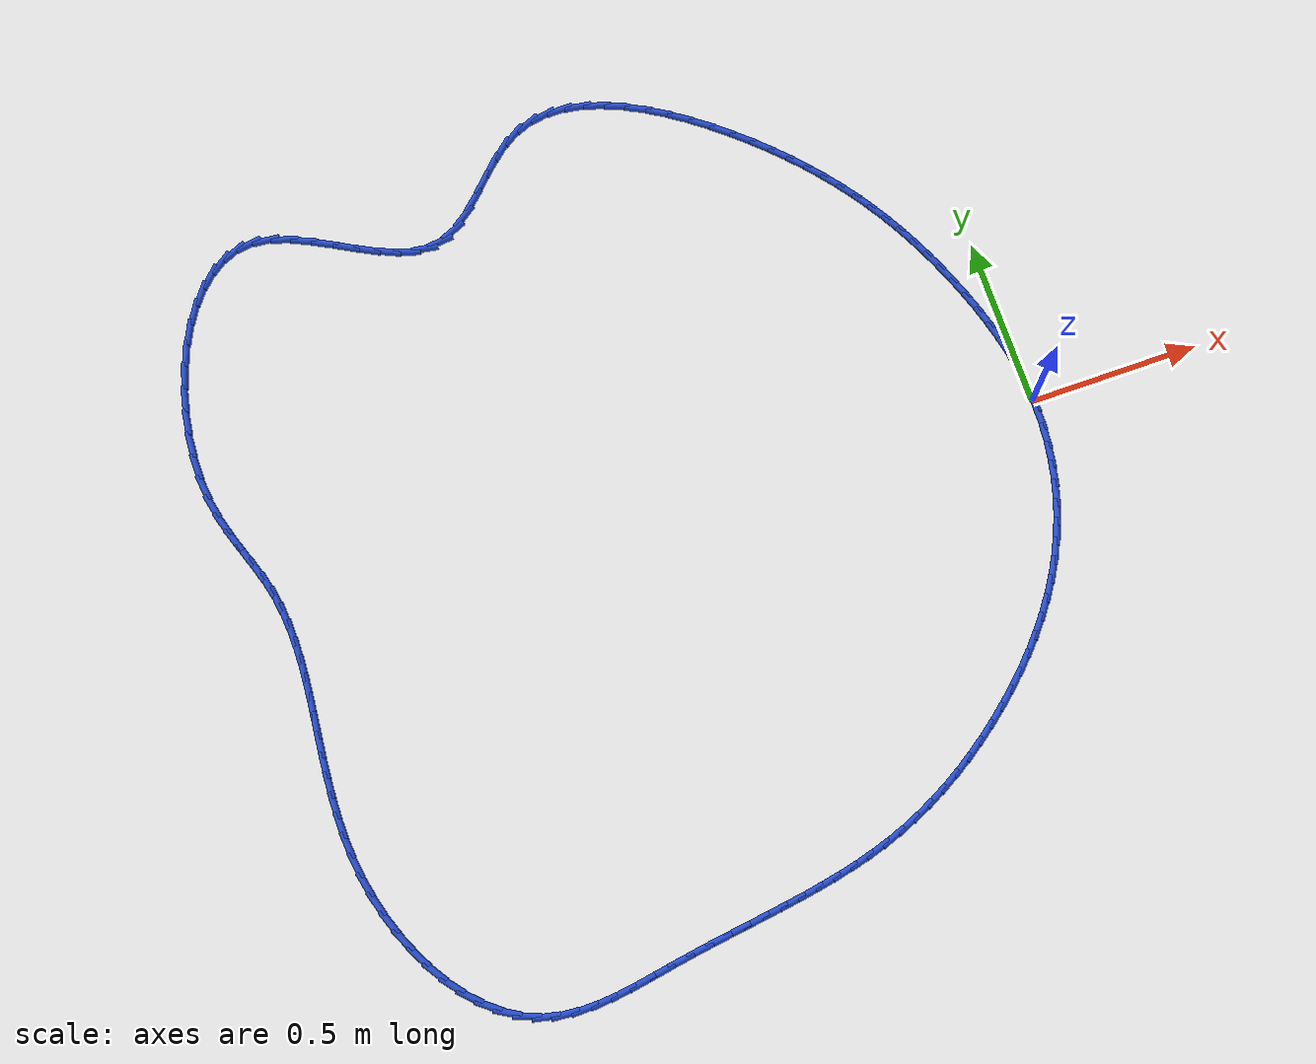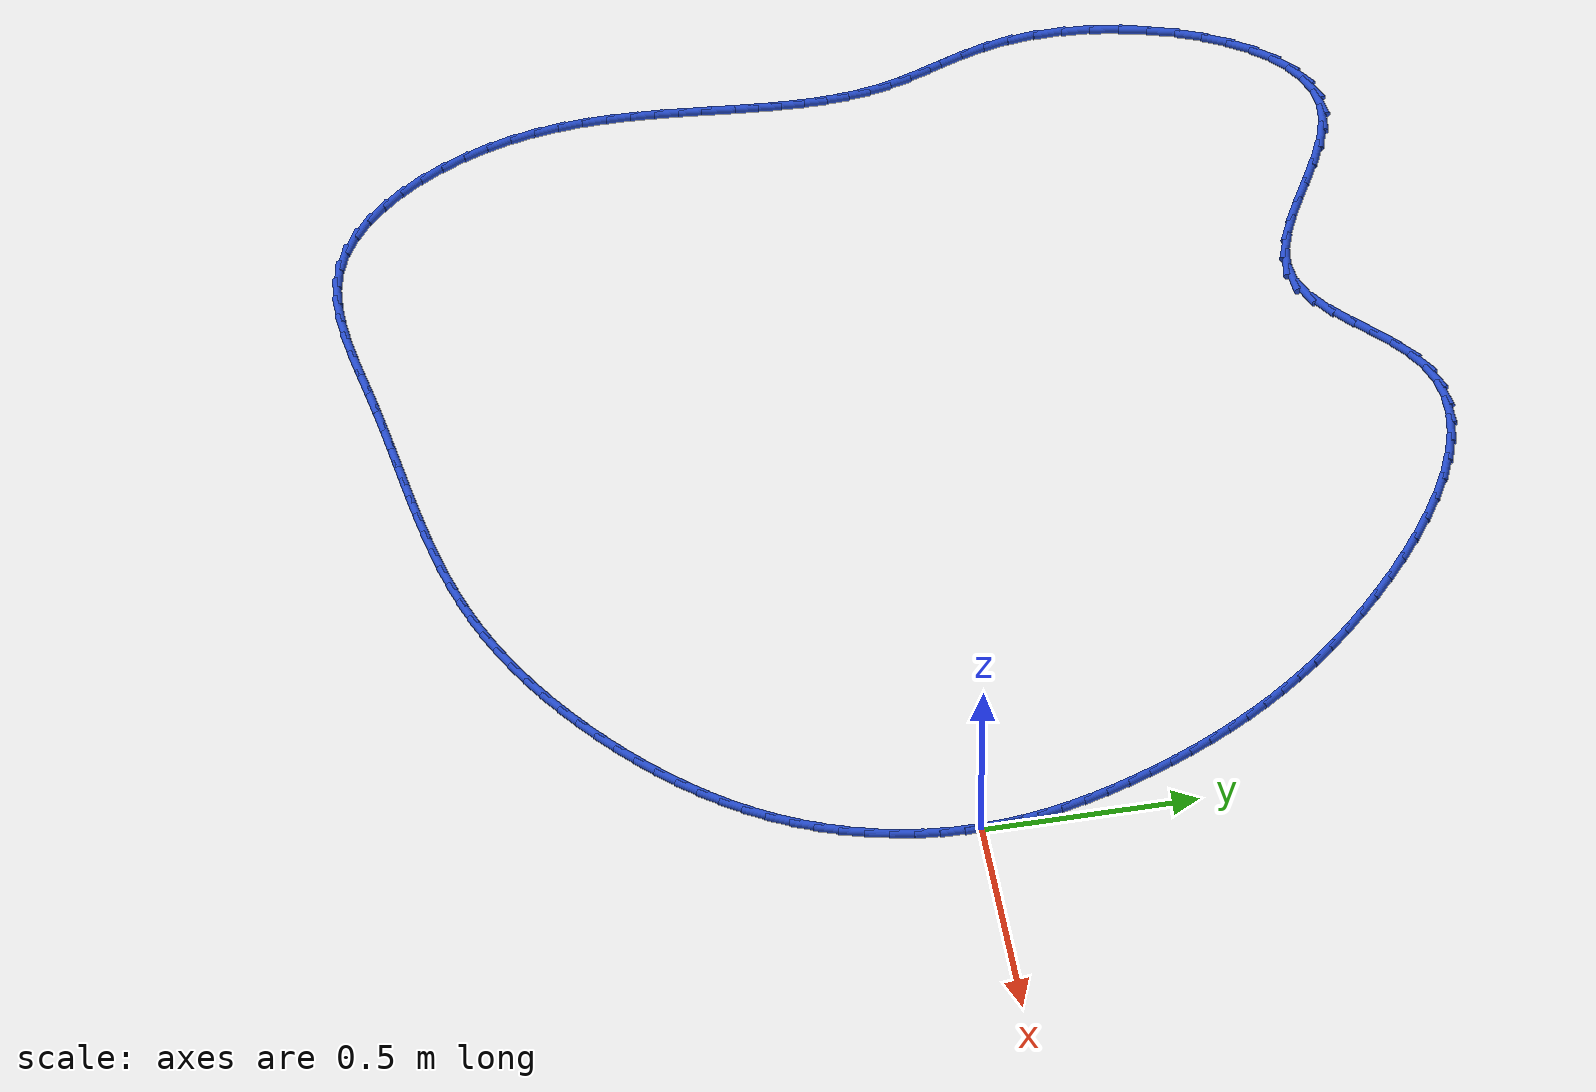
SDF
<sdf version="1.6">
 <world name="default">
  <light name="sun" type="directional">
   <pose>0 0 10 0 -0 0</pose>
   <diffuse>0.8 0.8 0.8 1</diffuse>
   <specular>0.2 0.2 0.2 1</specular>
   <attenuation>
    <range>1000</range>
    <constant>0.9</constant>
    <linear>0.01</linear>
    <quadratic>0.001</quadratic>
   </attenuation>
   <direction>-0.5 0.1 -0.9</direction>
  </light>
  <model name="ground_plane">
   <static>1</static>
   <link name="link">
    <collision name="collision">
     <geometry><plane><normal>0 0 1</normal><size>100 100</size></plane></geometry>
     <surface><friction><ode><mu>100</mu><mu2>50</mu2></ode></friction></surface>
    </collision>
    <visual name="visual">
     <cast_shadows>0</cast_shadows>
     <geometry><plane><normal>0 0 1</normal><size>100 100</size></plane></geometry>
     <material>
      <script><uri>file://media/materials/scripts/gazebo.material</uri><name>Gazebo/WhiteGlow</name></script>
     </material>
    </visual>
   </link>
  </model>
  <gravity>0 0 -9.8</gravity>
  <magnetic_field>6e-06 2.3e-05 -4.2e-05</magnetic_field>
  <atmosphere type="adiabatic"/>
  <physics name="default_physics" default="0" type="ode">
   <max_step_size>0.001</max_step_size>
   <real_time_factor>1</real_time_factor>
   <real_time_update_rate>1000</real_time_update_rate>
  </physics>
  <scene><ambient>0.4 0.4 0.4 1</ambient><background>0.7 0.7 0.7 1</background><shadows>1</shadows></scene>
  <spherical_coordinates>
   <surface_model>EARTH_WGS84</surface_model>
   <latitude_deg>0</latitude_deg>
   <longitude_deg>0</longitude_deg>
   <elevation>0</elevation>
   <heading_deg>0</heading_deg>
  </spherical_coordinates>
  <model name="line">
   <link name="link_0">
    <pose>-4.336808689942018e-17 6.938893903907228e-17 0.01 0 1.57 -1.5190994933021693</pose>
    <collision name="collision">
     <geometry><cylinder><radius>0.01</radius><length>0.08</length></cylinder></geometry>
    </collision>
    <visual name="visual">
     <material>
      <script><name>Gazebo/Blue</name><uri>file://media/materials/scripts/gazebo.material</uri></script>
     </material>
     <geometry><cylinder><radius>0.01</radius><length>0.08</length></cylinder></geometry>
    </visual>
   </link>
   <link name="link_1">
    <pose>-0.002924515269553467 0.05652008626312938 0.01 0 1.57 -1.4595664598543692</pose>
    <collision name="collision">
     <geometry><cylinder><radius>0.01</radius><length>0.08</length></cylinder></geometry>
    </collision>
    <visual name="visual">
     <material>
      <script><name>Gazebo/Blue</name><uri>file://media/materials/scripts/gazebo.material</uri></script>
     </material>
     <geometry><cylinder><radius>0.01</radius><length>0.08</length></cylinder></geometry>
    </visual>
   </link>
   <link name="link_2">
    <pose>-0.009207184599790863 0.11277060785166221 0.01 0 1.57 -1.4051411693131894</pose>
    <collision name="collision">
     <geometry><cylinder><radius>0.01</radius><length>0.08</length></cylinder></geometry>
    </collision>
    <visual name="visual">
     <material>
      <script><name>Gazebo/Blue</name><uri>file://media/materials/scripts/gazebo.material</uri></script>
     </material>
     <geometry><cylinder><radius>0.01</radius><length>0.08</length></cylinder></geometry>
    </visual>
   </link>
   <link name="link_3">
    <pose>-0.018545041480776108 0.168623290062879 0.01 0 1.57 -1.3556561289065543</pose>
    <collision name="collision">
     <geometry><cylinder><radius>0.01</radius><length>0.08</length></cylinder></geometry>
    </collision>
    <visual name="visual">
     <material>
      <script><name>Gazebo/Blue</name><uri>file://media/materials/scripts/gazebo.material</uri></script>
     </material>
     <geometry><cylinder><radius>0.01</radius><length>0.08</length></cylinder></geometry>
    </visual>
   </link>
   <link name="link_4">
    <pose>-0.030635119402573074 0.22394985819406033 0.01 0 1.57 -1.3108756740906422</pose>
    <collision name="collision">
     <geometry><cylinder><radius>0.01</radius><length>0.08</length></cylinder></geometry>
    </collision>
    <visual name="visual">
     <material>
      <script><name>Gazebo/Blue</name><uri>file://media/materials/scripts/gazebo.material</uri></script>
     </material>
     <geometry><cylinder><radius>0.01</radius><length>0.08</length></cylinder></geometry>
    </visual>
   </link>
   <link name="link_5">
    <pose>-0.04517445185524564 0.2786220375424868 0.01 0 1.57 -1.2705314752700712</pose>
    <collision name="collision">
     <geometry><cylinder><radius>0.01</radius><length>0.08</length></cylinder></geometry>
    </collision>
    <visual name="visual">
     <material>
      <script><name>Gazebo/Blue</name><uri>file://media/materials/scripts/gazebo.material</uri></script>
     </material>
     <geometry><cylinder><radius>0.01</radius><length>0.08</length></cylinder></geometry>
    </visual>
   </link>
   <link name="link_6">
    <pose>-0.0618600723288577 0.33251155340543886 0.01 0 1.57 -1.2343495490475975</pose>
    <collision name="collision">
     <geometry><cylinder><radius>0.01</radius><length>0.08</length></cylinder></geometry>
    </collision>
    <visual name="visual">
     <material>
      <script><name>Gazebo/Blue</name><uri>file://media/materials/scripts/gazebo.material</uri></script>
     </material>
     <geometry><cylinder><radius>0.01</radius><length>0.08</length></cylinder></geometry>
    </visual>
   </link>
   <link name="link_7">
    <pose>-0.08038901431347306 0.38549013108019714 0.01 0 1.57 -1.2020696993850095</pose>
    <collision name="collision">
     <geometry><cylinder><radius>0.01</radius><length>0.08</length></cylinder></geometry>
    </collision>
    <visual name="visual">
     <material>
      <script><name>Gazebo/Blue</name><uri>file://media/materials/scripts/gazebo.material</uri></script>
     </material>
     <geometry><cylinder><radius>0.01</radius><length>0.08</length></cylinder></geometry>
    </visual>
   </link>
   <link name="link_8">
    <pose>-0.10045833443613873 0.4374295067566357 0.01 0 1.57 -1.172305166254424</pose>
    <collision name="collision">
     <geometry><cylinder><radius>0.01</radius><length>0.08</length></cylinder></geometry>
    </collision>
    <visual name="visual">
     <material>
      <script><name>Gazebo/Blue</name><uri>file://media/materials/scripts/gazebo.material</uri></script>
     </material>
     <geometry><cylinder><radius>0.01</radius><length>0.08</length></cylinder></geometry>
    </visual>
   </link>
   <link name="link_9">
    <pose>-0.1218511733213149 0.48824194386113895 0.01 0 1.57 -1.1412504725120203</pose>
    <collision name="collision">
     <geometry><cylinder><radius>0.01</radius><length>0.08</length></cylinder></geometry>
    </collision>
    <visual name="visual">
     <material>
      <script><name>Gazebo/Blue</name><uri>file://media/materials/scripts/gazebo.material</uri></script>
     </material>
     <geometry><cylinder><radius>0.01</radius><length>0.08</length></cylinder></geometry>
    </visual>
   </link>
   <link name="link_10">
    <pose>-0.14463093248598793 0.5379716490362235 0.01 0 1.57 -1.1083312911811245</pose>
    <collision name="collision">
     <geometry><cylinder><radius>0.01</radius><length>0.08</length></cylinder></geometry>
    </collision>
    <visual name="visual">
     <material>
      <script><name>Gazebo/Blue</name><uri>file://media/materials/scripts/gazebo.material</uri></script>
     </material>
     <geometry><cylinder><radius>0.01</radius><length>0.08</length></cylinder></geometry>
    </visual>
   </link>
   <link name="link_11">
    <pose>-0.16891795223503722 0.5866896349719046 0.01 0 1.57 -1.0738031401811257</pose>
    <collision name="collision">
     <geometry><cylinder><radius>0.01</radius><length>0.08</length></cylinder></geometry>
    </collision>
    <visual name="visual">
     <material>
      <script><name>Gazebo/Blue</name><uri>file://media/materials/scripts/gazebo.material</uri></script>
     </material>
     <geometry><cylinder><radius>0.01</radius><length>0.08</length></cylinder></geometry>
    </visual>
   </link>
   <link name="link_12">
    <pose>-0.1948325728733422 0.6344669143581979 0.01 0 1.57 -1.0379664540874518</pose>
    <collision name="collision">
     <geometry><cylinder><radius>0.01</radius><length>0.08</length></cylinder></geometry>
    </collision>
    <visual name="visual">
     <material>
      <script><name>Gazebo/Blue</name><uri>file://media/materials/scripts/gazebo.material</uri></script>
     </material>
     <geometry><cylinder><radius>0.01</radius><length>0.08</length></cylinder></geometry>
    </visual>
   </link>
   <link name="link_13">
    <pose>-0.22249513470578242 0.681374499885119 0.01 0 1.57 -1.0011578783047872</pose>
    <collision name="collision">
     <geometry><cylinder><radius>0.01</radius><length>0.08</length></cylinder></geometry>
    </collision>
    <visual name="visual">
     <material>
      <script><name>Gazebo/Blue</name><uri>file://media/materials/scripts/gazebo.material</uri></script>
     </material>
     <geometry><cylinder><radius>0.01</radius><length>0.08</length></cylinder></geometry>
    </visual>
   </link>
   <link name="link_14">
    <pose>-0.25202597803723714 0.727483404242683 0.01 0 1.57 -0.9637385272499486</pose>
    <collision name="collision">
     <geometry><cylinder><radius>0.01</radius><length>0.08</length></cylinder></geometry>
    </collision>
    <visual name="visual">
     <material>
      <script><name>Gazebo/Blue</name><uri>file://media/materials/scripts/gazebo.material</uri></script>
     </material>
     <geometry><cylinder><radius>0.01</radius><length>0.08</length></cylinder></geometry>
    </visual>
   </link>
   <link name="link_15">
    <pose>-0.28354544317258595 0.7728646401209053 0.01 0 1.57 -0.9260801055363298</pose>
    <collision name="collision">
     <geometry><cylinder><radius>0.01</radius><length>0.08</length></cylinder></geometry>
    </collision>
    <visual name="visual">
     <material>
      <script><name>Gazebo/Blue</name><uri>file://media/materials/scripts/gazebo.material</uri></script>
     </material>
     <geometry><cylinder><radius>0.01</radius><length>0.08</length></cylinder></geometry>
    </visual>
   </link>
   <link name="link_16">
    <pose>-0.31717387041670825 0.8175892202098017 0.01 0 1.57 -0.8885501473949161</pose>
    <collision name="collision">
     <geometry><cylinder><radius>0.01</radius><length>0.08</length></cylinder></geometry>
    </collision>
    <visual name="visual">
     <material>
      <script><name>Gazebo/Blue</name><uri>file://media/materials/scripts/gazebo.material</uri></script>
     </material>
     <geometry><cylinder><radius>0.01</radius><length>0.08</length></cylinder></geometry>
    </visual>
   </link>
   <link name="link_17">
    <pose>-0.3530316000744835 0.8617281571993876 0.01 0 1.57 -0.8514977818351313</pose>
    <collision name="collision">
     <geometry><cylinder><radius>0.01</radius><length>0.08</length></cylinder></geometry>
    </collision>
    <visual name="visual">
     <material>
      <script><name>Gazebo/Blue</name><uri>file://media/materials/scripts/gazebo.material</uri></script>
     </material>
     <geometry><cylinder><radius>0.01</radius><length>0.08</length></cylinder></geometry>
    </visual>
   </link>
   <link name="link_18">
    <pose>-0.39123897245079114 0.9053524637796784 0.01 0 1.57 -0.8152413379001949</pose>
    <collision name="collision">
     <geometry><cylinder><radius>0.01</radius><length>0.08</length></cylinder></geometry>
    </collision>
    <visual name="visual">
     <material>
      <script><name>Gazebo/Blue</name><uri>file://media/materials/scripts/gazebo.material</uri></script>
     </material>
     <geometry><cylinder><radius>0.01</radius><length>0.08</length></cylinder></geometry>
    </visual>
   </link>
   <link name="link_19">
    <pose>-0.4319163278505107 0.9485331526406895 0.01 0 1.57 -0.7800587912551206</pose>
    <collision name="collision">
     <geometry><cylinder><radius>0.01</radius><length>0.08</length></cylinder></geometry>
    </collision>
    <visual name="visual">
     <material>
      <script><name>Gazebo/Blue</name><uri>file://media/materials/scripts/gazebo.material</uri></script>
     </material>
     <geometry><cylinder><radius>0.01</radius><length>0.08</length></cylinder></geometry>
    </visual>
   </link>
   <link name="link_20">
    <pose>-0.47518400657852156 0.9913412364724367 0.01 0 1.57 -0.7461815445896894</pose>
    <collision name="collision">
     <geometry><cylinder><radius>0.01</radius><length>0.08</length></cylinder></geometry>
    </collision>
    <visual name="visual">
     <material>
      <script><name>Gazebo/Blue</name><uri>file://media/materials/scripts/gazebo.material</uri></script>
     </material>
     <geometry><cylinder><radius>0.01</radius><length>0.08</length></cylinder></geometry>
    </visual>
   </link>
   <link name="link_21">
    <pose>-0.5211623421408822 1.0338477167215838 0.01 0 1.57 -0.7127710313288037</pose>
    <collision name="collision">
     <geometry><cylinder><radius>0.01</radius><length>0.08</length></cylinder></geometry>
    </collision>
    <visual name="visual">
     <material>
      <script><name>Gazebo/Blue</name><uri>file://media/materials/scripts/gazebo.material</uri></script>
     </material>
     <geometry><cylinder><radius>0.01</radius><length>0.08</length></cylinder></geometry>
    </visual>
   </link>
   <link name="link_22">
    <pose>-0.5698612925751441 1.0759410646355243 0.01 0 1.57 -0.6758368118899816</pose>
    <collision name="collision">
     <geometry><cylinder><radius>0.01</radius><length>0.08</length></cylinder></geometry>
    </collision>
    <visual name="visual">
     <material>
      <script><name>Gazebo/Blue</name><uri>file://media/materials/scripts/gazebo.material</uri></script>
     </material>
     <geometry><cylinder><radius>0.01</radius><length>0.08</length></cylinder></geometry>
    </visual>
   </link>
   <link name="link_23">
    <pose>-0.6209004555892221 1.1168642044961887 0.01 0 1.57 -0.6333698497305258</pose>
    <collision name="collision">
     <geometry><cylinder><radius>0.01</radius><length>0.08</length></cylinder></geometry>
    </collision>
    <visual name="visual">
     <material>
      <script><name>Gazebo/Blue</name><uri>file://media/materials/scripts/gazebo.material</uri></script>
     </material>
     <geometry><cylinder><radius>0.01</radius><length>0.08</length></cylinder></geometry>
    </visual>
   </link>
   <link name="link_24">
    <pose>-0.67381317327816 1.1557174178912688 0.01 0 1.57 -0.5837912353796403</pose>
    <collision name="collision">
     <geometry><cylinder><radius>0.01</radius><length>0.08</length></cylinder></geometry>
    </collision>
    <visual name="visual">
     <material>
      <script><name>Gazebo/Blue</name><uri>file://media/materials/scripts/gazebo.material</uri></script>
     </material>
     <geometry><cylinder><radius>0.01</radius><length>0.08</length></cylinder></geometry>
    </visual>
   </link>
   <link name="link_25">
    <pose>-0.7281327877370014 1.1916009864084562 0.01 0 1.57 -0.5250892704416449</pose>
    <collision name="collision">
     <geometry><cylinder><radius>0.01</radius><length>0.08</length></cylinder></geometry>
    </collision>
    <visual name="visual">
     <material>
      <script><name>Gazebo/Blue</name><uri>file://media/materials/scripts/gazebo.material</uri></script>
     </material>
     <geometry><cylinder><radius>0.01</radius><length>0.08</length></cylinder></geometry>
    </visual>
   </link>
   <link name="link_26">
    <pose>-0.7833926410607888 1.2236151916354423 0.01 0 1.57 -0.4546854858867576</pose>
    <collision name="collision">
     <geometry><cylinder><radius>0.01</radius><length>0.08</length></cylinder></geometry>
    </collision>
    <visual name="visual">
     <material>
      <script><name>Gazebo/Blue</name><uri>file://media/materials/scripts/gazebo.material</uri></script>
     </material>
     <geometry><cylinder><radius>0.01</radius><length>0.08</length></cylinder></geometry>
    </visual>
   </link>
   <link name="link_27">
    <pose>-0.8391260753445658 1.2508603151599191 0.01 0 1.57 -0.3693244661340358</pose>
    <collision name="collision">
     <geometry><cylinder><radius>0.01</radius><length>0.08</length></cylinder></geometry>
    </collision>
    <visual name="visual">
     <material>
      <script><name>Gazebo/Blue</name><uri>file://media/materials/scripts/gazebo.material</uri></script>
     </material>
     <geometry><cylinder><radius>0.01</radius><length>0.08</length></cylinder></geometry>
    </visual>
   </link>
   <link name="link_28">
    <pose>-0.8948664326833764 1.2724366385695778 0.01 0 1.57 -0.26509449051942185</pose>
    <collision name="collision">
     <geometry><cylinder><radius>0.01</radius><length>0.08</length></cylinder></geometry>
    </collision>
    <visual name="visual">
     <material>
      <script><name>Gazebo/Blue</name><uri>file://media/materials/scripts/gazebo.material</uri></script>
     </material>
     <geometry><cylinder><radius>0.01</radius><length>0.08</length></cylinder></geometry>
    </visual>
   </link>
   <link name="link_29">
    <pose>-0.9501470551722635 1.2874444434521104 0.01 0 1.57 -0.1378321899209526</pose>
    <collision name="collision">
     <geometry><cylinder><radius>0.01</radius><length>0.08</length></cylinder></geometry>
    </collision>
    <visual name="visual">
     <material>
      <script><name>Gazebo/Blue</name><uri>file://media/materials/scripts/gazebo.material</uri></script>
     </material>
     <geometry><cylinder><radius>0.01</radius><length>0.08</length></cylinder></geometry>
    </visual>
   </link>
   <link name="link_30">
    <pose>-1.00450128490627 1.2949840113952076 0.01 0 1.57 0.015640132584683365</pose>
    <collision name="collision">
     <geometry><cylinder><radius>0.01</radius><length>0.08</length></cylinder></geometry>
    </collision>
    <visual name="visual">
     <material>
      <script><name>Gazebo/Blue</name><uri>file://media/materials/scripts/gazebo.material</uri></script>
     </material>
     <geometry><cylinder><radius>0.01</radius><length>0.08</length></cylinder></geometry>
    </visual>
   </link>
   <link name="link_31">
    <pose>-1.05746246398044 1.2941556239865621 0.01 0 1.57 0.1950568718612323</pose>
    <collision name="collision">
     <geometry><cylinder><radius>0.01</radius><length>0.08</length></cylinder></geometry>
    </collision>
    <visual name="visual">
     <material>
      <script><name>Gazebo/Blue</name><uri>file://media/materials/scripts/gazebo.material</uri></script>
     </material>
     <geometry><cylinder><radius>0.01</radius><length>0.08</length></cylinder></geometry>
    </visual>
   </link>
   <link name="link_32">
    <pose>-1.1085639344898164 1.2840595628138647 0.01 0 1.57 0.3937511248027767</pose>
    <collision name="collision">
     <geometry><cylinder><radius>0.01</radius><length>0.08</length></cylinder></geometry>
    </collision>
    <visual name="visual">
     <material>
      <script><name>Gazebo/Blue</name><uri>file://media/materials/scripts/gazebo.material</uri></script>
     </material>
     <geometry><cylinder><radius>0.01</radius><length>0.08</length></cylinder></geometry>
    </visual>
   </link>
   <link name="link_33">
    <pose>-1.1573390385294433 1.2637961094648078 0.01 0 1.57 0.5896157293285393</pose>
    <collision name="collision">
     <geometry><cylinder><radius>0.01</radius><length>0.08</length></cylinder></geometry>
    </collision>
    <visual name="visual">
     <material>
      <script><name>Gazebo/Blue</name><uri>file://media/materials/scripts/gazebo.material</uri></script>
     </material>
     <geometry><cylinder><radius>0.01</radius><length>0.08</length></cylinder></geometry>
    </visual>
   </link>
   <link name="link_34">
    <pose>-1.2034526000015322 1.2329461715284347 0.01 0 1.57 0.7226743091859348</pose>
    <collision name="collision">
     <geometry><cylinder><radius>0.01</radius><length>0.08</length></cylinder></geometry>
    </collision>
    <visual name="visual">
     <material>
      <script><name>Gazebo/Blue</name><uri>file://media/materials/scripts/gazebo.material</uri></script>
     </material>
     <geometry><cylinder><radius>0.01</radius><length>0.08</length></cylinder></geometry>
    </visual>
   </link>
   <link name="link_35">
    <pose>-1.2474145833098154 1.19418003077087 0.01 0 1.57 0.7869786380744113</pose>
    <collision name="collision">
     <geometry><cylinder><radius>0.01</radius><length>0.08</length></cylinder></geometry>
    </collision>
    <visual name="visual">
     <material>
      <script><name>Gazebo/Blue</name><uri>file://media/materials/scripts/gazebo.material</uri></script>
     </material>
     <geometry><cylinder><radius>0.01</radius><length>0.08</length></cylinder></geometry>
    </visual>
   </link>
   <link name="link_36">
    <pose>-1.2900693237859646 1.151390247275858 0.01 0 1.57 0.7939183454649416</pose>
    <collision name="collision">
     <geometry><cylinder><radius>0.01</radius><length>0.08</length></cylinder></geometry>
    </collision>
    <visual name="visual">
     <material>
      <script><name>Gazebo/Blue</name><uri>file://media/materials/scripts/gazebo.material</uri></script>
     </material>
     <geometry><cylinder><radius>0.01</radius><length>0.08</length></cylinder></geometry>
    </visual>
   </link>
   <link name="link_37">
    <pose>-1.3322619856138638 1.1084724109601836 0.01 0 1.57 0.7435088943617072</pose>
    <collision name="collision">
     <geometry><cylinder><radius>0.01</radius><length>0.08</length></cylinder></geometry>
    </collision>
    <visual name="visual">
     <material>
      <script><name>Gazebo/Blue</name><uri>file://media/materials/scripts/gazebo.material</uri></script>
     </material>
     <geometry><cylinder><radius>0.01</radius><length>0.08</length></cylinder></geometry>
    </visual>
   </link>
   <link name="link_38">
    <pose>-1.3748377329773953 1.0693221117406349 0.01 0 1.57 0.6232452287033694</pose>
    <collision name="collision">
     <geometry><cylinder><radius>0.01</radius><length>0.08</length></cylinder></geometry>
    </collision>
    <visual name="visual">
     <material>
      <script><name>Gazebo/Blue</name><uri>file://media/materials/scripts/gazebo.material</uri></script>
     </material>
     <geometry><cylinder><radius>0.01</radius><length>0.08</length></cylinder></geometry>
    </visual>
   </link>
   <link name="link_39">
    <pose>-1.4186417300604435 1.037834939533997 0.01 0 1.57 0.409792824650364</pose>
    <collision name="collision">
     <geometry><cylinder><radius>0.01</radius><length>0.08</length></cylinder></geometry>
    </collision>
    <visual name="visual">
     <material>
      <script><name>Gazebo/Blue</name><uri>file://media/materials/scripts/gazebo.material</uri></script>
     </material>
     <geometry><cylinder><radius>0.01</radius><length>0.08</length></cylinder></geometry>
    </visual>
   </link>
   <link name="link_40">
    <pose>-1.4645191410468903 1.0179064842570567 0.01 0 1.57 0.10918027138400697</pose>
    <collision name="collision">
     <geometry><cylinder><radius>0.01</radius><length>0.08</length></cylinder></geometry>
    </collision>
    <visual name="visual">
     <material>
      <script><name>Gazebo/Blue</name><uri>file://media/materials/scripts/gazebo.material</uri></script>
     </material>
     <geometry><cylinder><radius>0.01</radius><length>0.08</length></cylinder></geometry>
    </visual>
   </link>
   <link name="link_41">
    <pose>-1.5131397471966364 1.012576879549368 0.01 0 1.57 -0.15075802445603628</pose>
    <collision name="collision">
     <geometry><cylinder><radius>0.01</radius><length>0.08</length></cylinder></geometry>
    </collision>
    <visual name="visual">
     <material>
      <script><name>Gazebo/Blue</name><uri>file://media/materials/scripts/gazebo.material</uri></script>
     </material>
     <geometry><cylinder><radius>0.01</radius><length>0.08</length></cylinder></geometry>
    </visual>
   </link>
   <link name="link_42">
    <pose>-1.5642412162302415 1.020339736731174 0.01 0 1.57 -0.32469964815816693</pose>
    <collision name="collision">
     <geometry><cylinder><radius>0.01</radius><length>0.08</length></cylinder></geometry>
    </collision>
    <visual name="visual">
     <material>
      <script><name>Gazebo/Blue</name><uri>file://media/materials/scripts/gazebo.material</uri></script>
     </material>
     <geometry><cylinder><radius>0.01</radius><length>0.08</length></cylinder></geometry>
    </visual>
   </link>
   <link name="link_43">
    <pose>-1.6172527603636977 1.0381841295563536 0.01 0 1.57 -0.42981292977353774</pose>
    <collision name="collision">
     <geometry><cylinder><radius>0.01</radius><length>0.08</length></cylinder></geometry>
    </collision>
    <visual name="visual">
     <material>
      <script><name>Gazebo/Blue</name><uri>file://media/materials/scripts/gazebo.material</uri></script>
     </material>
     <geometry><cylinder><radius>0.01</radius><length>0.08</length></cylinder></geometry>
    </visual>
   </link>
   <link name="link_44">
    <pose>-1.671603394225443 1.0630981680161329 0.01 0 1.57 -0.48393693534117505</pose>
    <collision name="collision">
     <geometry><cylinder><radius>0.01</radius><length>0.08</length></cylinder></geometry>
    </collision>
    <visual name="visual">
     <material>
      <script><name>Gazebo/Blue</name><uri>file://media/materials/scripts/gazebo.material</uri></script>
     </material>
     <geometry><cylinder><radius>0.01</radius><length>0.08</length></cylinder></geometry>
    </visual>
   </link>
   <link name="link_45">
    <pose>-1.7267221324439133 1.092069962101737 0.01 0 1.57 -0.4971898282523331</pose>
    <collision name="collision">
     <geometry><cylinder><radius>0.01</radius><length>0.08</length></cylinder></geometry>
    </collision>
    <visual name="visual">
     <material>
      <script><name>Gazebo/Blue</name><uri>file://media/materials/scripts/gazebo.material</uri></script>
     </material>
     <geometry><cylinder><radius>0.01</radius><length>0.08</length></cylinder></geometry>
    </visual>
   </link>
   <link name="link_46">
    <pose>-1.782037989647548 1.1220876218043914 0.01 0 1.57 -0.4720664089780338</pose>
    <collision name="collision">
     <geometry><cylinder><radius>0.01</radius><length>0.08</length></cylinder></geometry>
    </collision>
    <visual name="visual">
     <material>
      <script><name>Gazebo/Blue</name><uri>file://media/materials/scripts/gazebo.material</uri></script>
     </material>
     <geometry><cylinder><radius>0.01</radius><length>0.08</length></cylinder></geometry>
    </visual>
   </link>
   <link name="link_47">
    <pose>-1.8369799804647826 1.1501392571153215 0.01 0 1.57 -0.4038287956365215</pose>
    <collision name="collision">
     <geometry><cylinder><radius>0.01</radius><length>0.08</length></cylinder></geometry>
    </collision>
    <visual name="visual">
     <material>
      <script><name>Gazebo/Blue</name><uri>file://media/materials/scripts/gazebo.material</uri></script>
     </material>
     <geometry><cylinder><radius>0.01</radius><length>0.08</length></cylinder></geometry>
    </visual>
   </link>
   <link name="link_48">
    <pose>-1.8909771195240574 1.1732129780257539 0.01 0 1.57 -0.2798713648292134</pose>
    <collision name="collision">
     <geometry><cylinder><radius>0.01</radius><length>0.08</length></cylinder></geometry>
    </collision>
    <visual name="visual">
     <material>
      <script><name>Gazebo/Blue</name><uri>file://media/materials/scripts/gazebo.material</uri></script>
     </material>
     <geometry><cylinder><radius>0.01</radius><length>0.08</length></cylinder></geometry>
    </visual>
   </link>
   <link name="link_49">
    <pose>-1.9434584214538078 1.1882968945269123 0.01 0 1.57 -0.08105024340451306</pose>
    <collision name="collision">
     <geometry><cylinder><radius>0.01</radius><length>0.08</length></cylinder></geometry>
    </collision>
    <visual name="visual">
     <material>
      <script><name>Gazebo/Blue</name><uri>file://media/materials/scripts/gazebo.material</uri></script>
     </material>
     <geometry><cylinder><radius>0.01</radius><length>0.08</length></cylinder></geometry>
    </visual>
   </link>
   <link name="link_50">
    <pose>-1.9938537643696883 1.1923904169079258 0.01 0 1.57 0.1767937433057892</pose>
    <collision name="collision">
     <geometry><cylinder><radius>0.01</radius><length>0.08</length></cylinder></geometry>
    </collision>
    <visual name="visual">
     <material>
      <script><name>Gazebo/Blue</name><uri>file://media/materials/scripts/gazebo.material</uri></script>
     </material>
     <geometry><cylinder><radius>0.01</radius><length>0.08</length></cylinder></geometry>
    </visual>
   </link>
   <link name="link_51">
    <pose>-2.0416961822515827 1.183842937223414 0.01 0 1.57 0.4222356093087981</pose>
    <collision name="collision">
     <geometry><cylinder><radius>0.01</radius><length>0.08</length></cylinder></geometry>
    </collision>
    <visual name="visual">
     <material>
      <script><name>Gazebo/Blue</name><uri>file://media/materials/scripts/gazebo.material</uri></script>
     </material>
     <geometry><cylinder><radius>0.01</radius><length>0.08</length></cylinder></geometry>
    </visual>
   </link>
   <link name="link_52">
    <pose>-2.0867183438056847 1.1636164303635494 0.01 0 1.57 0.6308229185235149</pose>
    <collision name="collision">
     <geometry><cylinder><radius>0.01</radius><length>0.08</length></cylinder></geometry>
    </collision>
    <visual name="visual">
     <material>
      <script><name>Gazebo/Blue</name><uri>file://media/materials/scripts/gazebo.material</uri></script>
     </material>
     <geometry><cylinder><radius>0.01</radius><length>0.08</length></cylinder></geometry>
    </visual>
   </link>
   <link name="link_53">
    <pose>-2.1286757558103555 1.1329717488559319 0.01 0 1.57 0.8001049659863537</pose>
    <collision name="collision">
     <geometry><cylinder><radius>0.01</radius><length>0.08</length></cylinder></geometry>
    </collision>
    <visual name="visual">
     <material>
      <script><name>Gazebo/Blue</name><uri>file://media/materials/scripts/gazebo.material</uri></script>
     </material>
     <geometry><cylinder><radius>0.01</radius><length>0.08</length></cylinder></geometry>
    </visual>
   </link>
   <link name="link_54">
    <pose>-2.167323925043959 1.0931697452281612 0.01 0 1.57 0.9364739404567173</pose>
    <collision name="collision">
     <geometry><cylinder><radius>0.01</radius><length>0.08</length></cylinder></geometry>
    </collision>
    <visual name="visual">
     <material>
      <script><name>Gazebo/Blue</name><uri>file://media/materials/scripts/gazebo.material</uri></script>
     </material>
     <geometry><cylinder><radius>0.01</radius><length>0.08</length></cylinder></geometry>
    </visual>
   </link>
   <link name="link_55">
    <pose>-2.2024183582848584 1.0454712720078372 0.01 0 1.57 1.0482140510514923</pose>
    <collision name="collision">
     <geometry><cylinder><radius>0.01</radius><length>0.08</length></cylinder></geometry>
    </collision>
    <visual name="visual">
     <material>
      <script><name>Gazebo/Blue</name><uri>file://media/materials/scripts/gazebo.material</uri></script>
     </material>
     <geometry><cylinder><radius>0.01</radius><length>0.08</length></cylinder></geometry>
    </visual>
   </link>
   <link name="link_56">
    <pose>-2.2337145623114147 0.9911371817225597 0.01 0 1.57 1.1426002073141763</pose>
    <collision name="collision">
     <geometry><cylinder><radius>0.01</radius><length>0.08</length></cylinder></geometry>
    </collision>
    <visual name="visual">
     <material>
      <script><name>Gazebo/Blue</name><uri>file://media/materials/scripts/gazebo.material</uri></script>
     </material>
     <geometry><cylinder><radius>0.01</radius><length>0.08</length></cylinder></geometry>
    </visual>
   </link>
   <link name="link_57">
    <pose>-2.2609680439019915 0.9314283268999284 0.01 0 1.57 1.2253784912663193</pose>
    <collision name="collision">
     <geometry><cylinder><radius>0.01</radius><length>0.08</length></cylinder></geometry>
    </collision>
    <visual name="visual">
     <material>
      <script><name>Gazebo/Blue</name><uri>file://media/materials/scripts/gazebo.material</uri></script>
     </material>
     <geometry><cylinder><radius>0.01</radius><length>0.08</length></cylinder></geometry>
    </visual>
   </link>
   <link name="link_58">
    <pose>-2.283934309834951 0.8676055600675437 0.01 0 1.57 1.3010543503079308</pose>
    <collision name="collision">
     <geometry><cylinder><radius>0.01</radius><length>0.08</length></cylinder></geometry>
    </collision>
    <visual name="visual">
     <material>
      <script><name>Gazebo/Blue</name><uri>file://media/materials/scripts/gazebo.material</uri></script>
     </material>
     <geometry><cylinder><radius>0.01</radius><length>0.08</length></cylinder></geometry>
    </visual>
   </link>
   <link name="link_59">
    <pose>-2.302368866888657 0.8009297337530047 0.01 0 1.57 1.3733338892159097</pose>
    <collision name="collision">
     <geometry><cylinder><radius>0.01</radius><length>0.08</length></cylinder></geometry>
    </collision>
    <visual name="visual">
     <material>
      <script><name>Gazebo/Blue</name><uri>file://media/materials/scripts/gazebo.material</uri></script>
     </material>
     <geometry><cylinder><radius>0.01</radius><length>0.08</length></cylinder></geometry>
    </visual>
   </link>
   <link name="link_60">
    <pose>-2.3160272218414706 0.7326617004839118 0.01 0 1.57 1.445540973952849</pose>
    <collision name="collision">
     <geometry><cylinder><radius>0.01</radius><length>0.08</length></cylinder></geometry>
    </collision>
    <visual name="visual">
     <material>
      <script><name>Gazebo/Blue</name><uri>file://media/materials/scripts/gazebo.material</uri></script>
     </material>
     <geometry><cylinder><radius>0.01</radius><length>0.08</length></cylinder></geometry>
    </visual>
   </link>
   <link name="link_61">
    <pose>-2.324664881471755 0.6640623127878641 0.01 0 1.57 1.521000425694992</pose>
    <collision name="collision">
     <geometry><cylinder><radius>0.01</radius><length>0.08</length></cylinder></geometry>
    </collision>
    <visual name="visual">
     <material>
      <script><name>Gazebo/Blue</name><uri>file://media/materials/scripts/gazebo.material</uri></script>
     </material>
     <geometry><cylinder><radius>0.01</radius><length>0.08</length></cylinder></geometry>
    </visual>
   </link>
   <link name="link_62">
    <pose>-2.328037352557874 0.5963924231924627 0.01 0 1.57 -1.538168543299632</pose>
    <collision name="collision">
     <geometry><cylinder><radius>0.01</radius><length>0.08</length></cylinder></geometry>
    </collision>
    <visual name="visual">
     <material>
      <script><name>Gazebo/Blue</name><uri>file://media/materials/scripts/gazebo.material</uri></script>
     </material>
     <geometry><cylinder><radius>0.01</radius><length>0.08</length></cylinder></geometry>
    </visual>
   </link>
   <link name="link_63">
    <pose>-2.3259001418781886 0.530912884225306 0.01 0 1.57 -1.4443915290629803</pose>
    <collision name="collision">
     <geometry><cylinder><radius>0.01</radius><length>0.08</length></cylinder></geometry>
    </collision>
    <visual name="visual">
     <material>
      <script><name>Gazebo/Blue</name><uri>file://media/materials/scripts/gazebo.material</uri></script>
     </material>
     <geometry><cylinder><radius>0.01</radius><length>0.08</length></cylinder></geometry>
    </visual>
   </link>
   <link name="link_64">
    <pose>-2.3180164360766895 0.4688766951300189 0.01 0 1.57 -1.3480493920339112</pose>
    <collision name="collision">
     <geometry><cylinder><radius>0.01</radius><length>0.08</length></cylinder></geometry>
    </collision>
    <visual name="visual">
     <material>
      <script><name>Gazebo/Blue</name><uri>file://media/materials/scripts/gazebo.material</uri></script>
     </material>
     <geometry><cylinder><radius>0.01</radius><length>0.08</length></cylinder></geometry>
    </visual>
   </link>
   <link name="link_65">
    <pose>-2.3048632987177053 0.41080685823991936 0.01 0 1.57 -1.2760984443607262</pose>
    <collision name="collision">
     <geometry><cylinder><radius>0.01</radius><length>0.08</length></cylinder></geometry>
    </collision>
    <visual name="visual">
     <material>
      <script><name>Gazebo/Blue</name><uri>file://media/materials/scripts/gazebo.material</uri></script>
     </material>
     <geometry><cylinder><radius>0.01</radius><length>0.08</length></cylinder></geometry>
    </visual>
   </link>
   <link name="link_66">
    <pose>-2.288201294398937 0.35591389223457726 0.01 0 1.57 -1.236639593016519</pose>
    <collision name="collision">
     <geometry><cylinder><radius>0.01</radius><length>0.08</length></cylinder></geometry>
    </collision>
    <visual name="visual">
     <material>
      <script><name>Gazebo/Blue</name><uri>file://media/materials/scripts/gazebo.material</uri></script>
     </material>
     <geometry><cylinder><radius>0.01</radius><length>0.08</length></cylinder></geometry>
    </visual>
   </link>
   <link name="link_67">
    <pose>-2.269925033604761 0.3032712430288806 0.01 0 1.57 -1.233526262270694</pose>
    <collision name="collision">
     <geometry><cylinder><radius>0.01</radius><length>0.08</length></cylinder></geometry>
    </collision>
    <visual name="visual">
     <material>
      <script><name>Gazebo/Blue</name><uri>file://media/materials/scripts/gazebo.material</uri></script>
     </material>
     <geometry><cylinder><radius>0.01</radius><length>0.08</length></cylinder></geometry>
    </visual>
   </link>
   <link name="link_68">
    <pose>-2.2519291268195554 0.25195235653771625 0.01 0 1.57 -1.2695597313269982</pose>
    <collision name="collision">
     <geometry><cylinder><radius>0.01</radius><length>0.08</length></cylinder></geometry>
    </collision>
    <visual name="visual">
     <material>
      <script><name>Gazebo/Blue</name><uri>file://media/materials/scripts/gazebo.material</uri></script>
     </material>
     <geometry><cylinder><radius>0.01</radius><length>0.08</length></cylinder></geometry>
    </visual>
   </link>
   <link name="link_69">
    <pose>-2.2361081845276973 0.20103067867597263 0.01 0 1.57 -1.3428761525967992</pose>
    <collision name="collision">
     <geometry><cylinder><radius>0.01</radius><length>0.08</length></cylinder></geometry>
    </collision>
    <visual name="visual">
     <material>
      <script><name>Gazebo/Blue</name><uri>file://media/materials/scripts/gazebo.material</uri></script>
     </material>
     <geometry><cylinder><radius>0.01</radius><length>0.08</length></cylinder></geometry>
    </visual>
   </link>
   <link name="link_70">
    <pose>-2.2241891853914924 0.14964473601878212 0.01 0 1.57 -1.4225137728268966</pose>
    <collision name="collision">
     <geometry><cylinder><radius>0.01</radius><length>0.08</length></cylinder></geometry>
    </collision>
    <visual name="visual">
     <material>
      <script><name>Gazebo/Blue</name><uri>file://media/materials/scripts/gazebo.material</uri></script>
     </material>
     <geometry><cylinder><radius>0.01</radius><length>0.08</length></cylinder></geometry>
    </visual>
   </link>
   <link name="link_71">
    <pose>-2.216401991564229 0.0975142892391193 0.01 0 1.57 -1.4912507556115309</pose>
    <collision name="collision">
     <geometry><cylinder><radius>0.01</radius><length>0.08</length></cylinder></geometry>
    </collision>
    <visual name="visual">
     <material>
      <script><name>Gazebo/Blue</name><uri>file://media/materials/scripts/gazebo.material</uri></script>
     </material>
     <geometry><cylinder><radius>0.01</radius><length>0.08</length></cylinder></geometry>
    </visual>
   </link>
   <link name="link_72">
    <pose>-2.2121891562904112 0.044664760446835025 0.01 0 1.57 -1.5483322867702076</pose>
    <collision name="collision">
     <geometry><cylinder><radius>0.01</radius><length>0.08</length></cylinder></geometry>
    </collision>
    <visual name="visual">
     <material>
      <script><name>Gazebo/Blue</name><uri>file://media/materials/scripts/gazebo.material</uri></script>
     </material>
     <geometry><cylinder><radius>0.01</radius><length>0.08</length></cylinder></geometry>
    </visual>
   </link>
   <link name="link_73">
    <pose>-2.210986218774197 -0.008875705147253273 0.01 0 1.57 1.547877374138946</pose>
    <collision name="collision">
     <geometry><cylinder><radius>0.01</radius><length>0.08</length></cylinder></geometry>
    </collision>
    <visual name="visual">
     <material>
      <script><name>Gazebo/Blue</name><uri>file://media/materials/scripts/gazebo.material</uri></script>
     </material>
     <geometry><cylinder><radius>0.01</radius><length>0.08</length></cylinder></geometry>
    </visual>
   </link>
   <link name="link_74">
    <pose>-2.212228718219742 -0.06307896233232571 0.01 0 1.57 1.5138994691836993</pose>
    <collision name="collision">
     <geometry><cylinder><radius>0.01</radius><length>0.08</length></cylinder></geometry>
    </collision>
    <visual name="visual">
     <material>
      <script><name>Gazebo/Blue</name><uri>file://media/materials/scripts/gazebo.material</uri></script>
     </material>
     <geometry><cylinder><radius>0.01</radius><length>0.08</length></cylinder></geometry>
    </visual>
   </link>
   <link name="link_75">
    <pose>-2.215352193831203 -0.11791686589756473 0.01 0 1.57 1.4908867956658542</pose>
    <collision name="collision">
     <geometry><cylinder><radius>0.01</radius><length>0.08</length></cylinder></geometry>
    </collision>
    <visual name="visual">
     <material>
      <script><name>Gazebo/Blue</name><uri>file://media/materials/scripts/gazebo.material</uri></script>
     </material>
     <geometry><cylinder><radius>0.01</radius><length>0.08</length></cylinder></geometry>
    </visual>
   </link>
   <link name="link_76">
    <pose>-2.219792184812738 -0.17336127063215212 0.01 0 1.57 1.4783828751766026</pose>
    <collision name="collision">
     <geometry><cylinder><radius>0.01</radius><length>0.08</length></cylinder></geometry>
    </collision>
    <visual name="visual">
     <material>
      <script><name>Gazebo/Blue</name><uri>file://media/materials/scripts/gazebo.material</uri></script>
     </material>
     <geometry><cylinder><radius>0.01</radius><length>0.08</length></cylinder></geometry>
    </visual>
   </link>
   <link name="link_77">
    <pose>-2.224984230368502 -0.22938403132526952 0.01 0 1.57 1.4759893635850043</pose>
    <collision name="collision">
     <geometry><cylinder><radius>0.01</radius><length>0.08</length></cylinder></geometry>
    </collision>
    <visual name="visual">
     <material>
      <script><name>Gazebo/Blue</name><uri>file://media/materials/scripts/gazebo.material</uri></script>
     </material>
     <geometry><cylinder><radius>0.01</radius><length>0.08</length></cylinder></geometry>
    </visual>
   </link>
   <link name="link_78">
    <pose>-2.230363869702654 -0.28595700276609953 0.01 0 1.57 1.483397698757285</pose>
    <collision name="collision">
     <geometry><cylinder><radius>0.01</radius><length>0.08</length></cylinder></geometry>
    </collision>
    <visual name="visual">
     <material>
      <script><name>Gazebo/Blue</name><uri>file://media/materials/scripts/gazebo.material</uri></script>
     </material>
     <geometry><cylinder><radius>0.01</radius><length>0.08</length></cylinder></geometry>
    </visual>
   </link>
   <link name="link_79">
    <pose>-2.23536664201935 -0.3430520397438222 0.01 0 1.57 1.5003881930009453</pose>
    <collision name="collision">
     <geometry><cylinder><radius>0.01</radius><length>0.08</length></cylinder></geometry>
    </collision>
    <visual name="visual">
     <material>
      <script><name>Gazebo/Blue</name><uri>file://media/materials/scripts/gazebo.material</uri></script>
     </material>
     <geometry><cylinder><radius>0.01</radius><length>0.08</length></cylinder></geometry>
    </visual>
   </link>
   <link name="link_80">
    <pose>-2.2394280865227465 -0.40064099704762013 0.01 0 1.57 1.5268032388371462</pose>
    <collision name="collision">
     <geometry><cylinder><radius>0.01</radius><length>0.08</length></cylinder></geometry>
    </collision>
    <visual name="visual">
     <material>
      <script><name>Gazebo/Blue</name><uri>file://media/materials/scripts/gazebo.material</uri></script>
     </material>
     <geometry><cylinder><radius>0.01</radius><length>0.08</length></cylinder></geometry>
    </visual>
   </link>
   <link name="link_81">
    <pose>-2.2419837424170006 -0.45869572946667475 0.01 0 1.57 1.5624978870059154</pose>
    <collision name="collision">
     <geometry><cylinder><radius>0.01</radius><length>0.08</length></cylinder></geometry>
    </collision>
    <visual name="visual">
     <material>
      <script><name>Gazebo/Blue</name><uri>file://media/materials/scripts/gazebo.material</uri></script>
     </material>
     <geometry><cylinder><radius>0.01</radius><length>0.08</length></cylinder></geometry>
    </visual>
   </link>
   <link name="link_82">
    <pose>-2.2424691489062694 -0.517188091790169 0.01 0 1.57 -1.5343229281393642</pose>
    <collision name="collision">
     <geometry><cylinder><radius>0.01</radius><length>0.08</length></cylinder></geometry>
    </collision>
    <visual name="visual">
     <material>
      <script><name>Gazebo/Blue</name><uri>file://media/materials/scripts/gazebo.material</uri></script>
     </material>
     <geometry><cylinder><radius>0.01</radius><length>0.08</length></cylinder></geometry>
    </visual>
   </link>
   <link name="link_83">
    <pose>-2.2403198451947097 -0.5760899388072827 0.01 0 1.57 -1.4808208344254752</pose>
    <collision name="collision">
     <geometry><cylinder><radius>0.01</radius><length>0.08</length></cylinder></geometry>
    </collision>
    <visual name="visual">
     <material>
      <script><name>Gazebo/Blue</name><uri>file://media/materials/scripts/gazebo.material</uri></script>
     </material>
     <geometry><cylinder><radius>0.01</radius><length>0.08</length></cylinder></geometry>
    </visual>
   </link>
   <link name="link_84">
    <pose>-2.2349713704864786 -0.6353731253071986 0.01 0 1.57 -1.4191745720131188</pose>
    <collision name="collision">
     <geometry><cylinder><radius>0.01</radius><length>0.08</length></cylinder></geometry>
    </collision>
    <visual name="visual">
     <material>
      <script><name>Gazebo/Blue</name><uri>file://media/materials/scripts/gazebo.material</uri></script>
     </material>
     <geometry><cylinder><radius>0.01</radius><length>0.08</length></cylinder></geometry>
    </visual>
   </link>
   <link name="link_85">
    <pose>-2.2258592639857326 -0.695009506079098 0.01 0 1.57 -1.3512575477417346</pose>
    <collision name="collision">
     <geometry><cylinder><radius>0.01</radius><length>0.08</length></cylinder></geometry>
    </collision>
    <visual name="visual">
     <material>
      <script><name>Gazebo/Blue</name><uri>file://media/materials/scripts/gazebo.material</uri></script>
     </material>
     <geometry><cylinder><radius>0.01</radius><length>0.08</length></cylinder></geometry>
    </visual>
   </link>
   <link name="link_86">
    <pose>-2.2124997282467356 -0.7548814425891418 0.01 0 1.57 -1.2827129853121926</pose>
    <collision name="collision">
     <geometry><cylinder><radius>0.01</radius><length>0.08</length></cylinder></geometry>
    </collision>
    <visual name="visual">
     <material>
      <script><name>Gazebo/Blue</name><uri>file://media/materials/scripts/gazebo.material</uri></script>
     </material>
     <geometry><cylinder><radius>0.01</radius><length>0.08</length></cylinder></geometry>
    </visual>
   </link>
   <link name="link_87">
    <pose>-2.194877014223793 -0.8143520120610287 0.01 0 1.57 -1.213664323409909</pose>
    <collision name="collision">
     <geometry><cylinder><radius>0.01</radius><length>0.08</length></cylinder></geometry>
    </collision>
    <visual name="visual">
     <material>
      <script><name>Gazebo/Blue</name><uri>file://media/materials/scripts/gazebo.material</uri></script>
     </material>
     <geometry><cylinder><radius>0.01</radius><length>0.08</length></cylinder></geometry>
    </visual>
   </link>
   <link name="link_88">
    <pose>-2.1731437718123954 -0.8725974586546212 0.01 0 1.57 -1.1420013454729285</pose>
    <collision name="collision">
     <geometry><cylinder><radius>0.01</radius><length>0.08</length></cylinder></geometry>
    </collision>
    <visual name="visual">
     <material>
      <script><name>Gazebo/Blue</name><uri>file://media/materials/scripts/gazebo.material</uri></script>
     </material>
     <geometry><cylinder><radius>0.01</radius><length>0.08</length></cylinder></geometry>
    </visual>
   </link>
   <link name="link_89">
    <pose>-2.147452872990396 -0.9287937801367321 0.01 0 1.57 -1.0655385041338</pose>
    <collision name="collision">
     <geometry><cylinder><radius>0.01</radius><length>0.08</length></cylinder></geometry>
    </collision>
    <visual name="visual">
     <material>
      <script><name>Gazebo/Blue</name><uri>file://media/materials/scripts/gazebo.material</uri></script>
     </material>
     <geometry><cylinder><radius>0.01</radius><length>0.08</length></cylinder></geometry>
    </visual>
   </link>
   <link name="link_90">
    <pose>-2.117957189735652 -0.9821169742741727 0.01 0 1.57 -0.9819076566004005</pose>
    <collision name="collision">
     <geometry><cylinder><radius>0.01</radius><length>0.08</length></cylinder></geometry>
    </collision>
    <visual name="visual">
     <material>
      <script><name>Gazebo/Blue</name><uri>file://media/materials/scripts/gazebo.material</uri></script>
     </material>
     <geometry><cylinder><radius>0.01</radius><length>0.08</length></cylinder></geometry>
    </visual>
   </link>
   <link name="link_91">
    <pose>-2.084809594026017 -1.031743038833756 0.01 0 1.57 -0.8884947514427498</pose>
    <collision name="collision">
     <geometry><cylinder><radius>0.01</radius><length>0.08</length></cylinder></geometry>
    </collision>
    <visual name="visual">
     <material>
      <script><name>Gazebo/Blue</name><uri>file://media/materials/scripts/gazebo.material</uri></script>
     </material>
     <geometry><cylinder><radius>0.01</radius><length>0.08</length></cylinder></geometry>
    </visual>
   </link>
   <link name="link_92">
    <pose>-2.0481629578393474 -1.0768479715822918 0.01 0 1.57 -0.7824765619865748</pose>
    <collision name="collision">
     <geometry><cylinder><radius>0.01</radius><length>0.08</length></cylinder></geometry>
    </collision>
    <visual name="visual">
     <material>
      <script><name>Gazebo/Blue</name><uri>file://media/materials/scripts/gazebo.material</uri></script>
     </material>
     <geometry><cylinder><radius>0.01</radius><length>0.08</length></cylinder></geometry>
    </visual>
   </link>
   <link name="link_93">
    <pose>-2.0081701531534994 -1.1166077702865933 0.01 0 1.57 -0.6610644147449508</pose>
    <collision name="collision">
     <geometry><cylinder><radius>0.01</radius><length>0.08</length></cylinder></geometry>
    </collision>
    <visual name="visual">
     <material>
      <script><name>Gazebo/Blue</name><uri>file://media/materials/scripts/gazebo.material</uri></script>
     </material>
     <geometry><cylinder><radius>0.01</radius><length>0.08</length></cylinder></geometry>
    </visual>
   </link>
   <link name="link_94">
    <pose>-1.9649840519463266 -1.1501984327134718 0.01 0 1.57 -0.5221150272227103</pose>
    <collision name="collision">
     <geometry><cylinder><radius>0.01</radius><length>0.08</length></cylinder></geometry>
    </collision>
    <visual name="visual">
     <material>
      <script><name>Gazebo/Blue</name><uri>file://media/materials/scripts/gazebo.material</uri></script>
     </material>
     <geometry><cylinder><radius>0.01</radius><length>0.08</length></cylinder></geometry>
    </visual>
   </link>
   <link name="link_95">
    <pose>-1.9187575261956848 -1.1767959566297401 0.01 0 1.57 -0.3652760010253665</pose>
    <collision name="collision">
     <geometry><cylinder><radius>0.01</radius><length>0.08</length></cylinder></geometry>
    </collision>
    <visual name="visual">
     <material>
      <script><name>Gazebo/Blue</name><uri>file://media/materials/scripts/gazebo.material</uri></script>
     </material>
     <geometry><cylinder><radius>0.01</radius><length>0.08</length></cylinder></geometry>
    </visual>
   </link>
   <link name="link_96">
    <pose>-1.8696438001111093 -1.1955789311458886 0.01 0 1.57 -0.20475220792065918</pose>
    <collision name="collision">
     <geometry><cylinder><radius>0.01</radius><length>0.08</length></cylinder></geometry>
    </collision>
    <visual name="visual">
     <material>
      <script><name>Gazebo/Blue</name><uri>file://media/materials/scripts/gazebo.material</uri></script>
     </material>
     <geometry><cylinder><radius>0.01</radius><length>0.08</length></cylinder></geometry>
    </visual>
   </link>
   <link name="link_97">
    <pose>-1.8178780322901191 -1.2063287309003432 0.01 0 1.57 -0.07155175958120556</pose>
    <collision name="collision">
     <geometry><cylinder><radius>0.01</radius><length>0.08</length></cylinder></geometry>
    </collision>
    <visual name="visual">
     <material>
      <script><name>Gazebo/Blue</name><uri>file://media/materials/scripts/gazebo.material</uri></script>
     </material>
     <geometry><cylinder><radius>0.01</radius><length>0.08</length></cylinder></geometry>
    </visual>
   </link>
   <link name="link_98">
    <pose>-1.7638818893299728 -1.2101988567638855 0.01 0 1.57 0.02986066715614949</pose>
    <collision name="collision">
     <geometry><cylinder><radius>0.01</radius><length>0.08</length></cylinder></geometry>
    </collision>
    <visual name="visual">
     <material>
      <script><name>Gazebo/Blue</name><uri>file://media/materials/scripts/gazebo.material</uri></script>
     </material>
     <geometry><cylinder><radius>0.01</radius><length>0.08</length></cylinder></geometry>
    </visual>
   </link>
   <link name="link_99">
    <pose>-1.7081028574066826 -1.2085327624316449 0.01 0 1.57 0.10222352634762076</pose>
    <collision name="collision">
     <geometry><cylinder><radius>0.01</radius><length>0.08</length></cylinder></geometry>
    </collision>
    <visual name="visual">
     <material>
      <script><name>Gazebo/Blue</name><uri>file://media/materials/scripts/gazebo.material</uri></script>
     </material>
     <geometry><cylinder><radius>0.01</radius><length>0.08</length></cylinder></geometry>
    </visual>
   </link>
   <link name="link_100">
    <pose>-1.6509884226962572 -1.2026739015987473 0.01 0 1.57 0.1490218162277606</pose>
    <collision name="collision">
     <geometry><cylinder><radius>0.01</radius><length>0.08</length></cylinder></geometry>
    </collision>
    <visual name="visual">
     <material>
      <script><name>Gazebo/Blue</name><uri>file://media/materials/scripts/gazebo.material</uri></script>
     </material>
     <geometry><cylinder><radius>0.01</radius><length>0.08</length></cylinder></geometry>
    </visual>
   </link>
   <link name="link_101">
    <pose>-1.59298607137471 -1.1939657279603213 0.01 0 1.57 0.17302228930949384</pose>
    <collision name="collision">
     <geometry><cylinder><radius>0.01</radius><length>0.08</length></cylinder></geometry>
    </collision>
    <visual name="visual">
     <material>
      <script><name>Gazebo/Blue</name><uri>file://media/materials/scripts/gazebo.material</uri></script>
     </material>
     <geometry><cylinder><radius>0.01</radius><length>0.08</length></cylinder></geometry>
    </visual>
   </link>
   <link name="link_102">
    <pose>-1.5345432896180506 -1.1837516952114941 0.01 0 1.57 0.17573837652674507</pose>
    <collision name="collision">
     <geometry><cylinder><radius>0.01</radius><length>0.08</length></cylinder></geometry>
    </collision>
    <visual name="visual">
     <material>
      <script><name>Gazebo/Blue</name><uri>file://media/materials/scripts/gazebo.material</uri></script>
     </material>
     <geometry><cylinder><radius>0.01</radius><length>0.08</length></cylinder></geometry>
    </visual>
   </link>
   <link name="link_103">
    <pose>-1.4761075625117936 -1.1733752528752528 0.01 0 1.57 0.16204192280867324</pose>
    <collision name="collision">
     <geometry><cylinder><radius>0.01</radius><length>0.08</length></cylinder></geometry>
    </collision>
    <visual name="visual">
     <material>
      <script><name>Gazebo/Blue</name><uri>file://media/materials/scripts/gazebo.material</uri></script>
     </material>
     <geometry><cylinder><radius>0.01</radius><length>0.08</length></cylinder></geometry>
    </visual>
   </link>
   <link name="link_104">
    <pose>-1.4180490803121648 -1.1638841276612626 0.01 0 1.57 0.1491722900026604</pose>
    <collision name="collision">
     <geometry><cylinder><radius>0.01</radius><length>0.08</length></cylinder></geometry>
    </collision>
    <visual name="visual">
     <material>
      <script><name>Gazebo/Blue</name><uri>file://media/materials/scripts/gazebo.material</uri></script>
     </material>
     <geometry><cylinder><radius>0.01</radius><length>0.08</length></cylinder></geometry>
    </visual>
   </link>
   <link name="link_105">
    <pose>-1.3604509735850179 -1.155227782656479 0.01 0 1.57 0.1413279113378697</pose>
    <collision name="collision">
     <geometry><cylinder><radius>0.01</radius><length>0.08</length></cylinder></geometry>
    </collision>
    <visual name="visual">
     <material>
      <script><name>Gazebo/Blue</name><uri>file://media/materials/scripts/gazebo.material</uri></script>
     </material>
     <geometry><cylinder><radius>0.01</radius><length>0.08</length></cylinder></geometry>
    </visual>
   </link>
   <link name="link_106">
    <pose>-1.3033297475137788 -1.147100778443882 0.01 0 1.57 0.13866647746486765</pose>
    <collision name="collision">
     <geometry><cylinder><radius>0.01</radius><length>0.08</length></cylinder></geometry>
    </collision>
    <visual name="visual">
     <material>
      <script><name>Gazebo/Blue</name><uri>file://media/materials/scripts/gazebo.material</uri></script>
     </material>
     <geometry><cylinder><radius>0.01</radius><length>0.08</length></cylinder></geometry>
    </visual>
   </link>
   <link name="link_107">
    <pose>-1.2467019072818744 -1.1391976756064524 0.01 0 1.57 0.1413345365285853</pose>
    <collision name="collision">
     <geometry><cylinder><radius>0.01</radius><length>0.08</length></cylinder></geometry>
    </collision>
    <visual name="visual">
     <material>
      <script><name>Gazebo/Blue</name><uri>file://media/materials/scripts/gazebo.material</uri></script>
     </material>
     <geometry><cylinder><radius>0.01</radius><length>0.08</length></cylinder></geometry>
    </visual>
   </link>
   <link name="link_108">
    <pose>-1.1905839580727309 -1.1312130347271696 0.01 0 1.57 0.1494684339492015</pose>
    <collision name="collision">
     <geometry><cylinder><radius>0.01</radius><length>0.08</length></cylinder></geometry>
    </collision>
    <visual name="visual">
     <material>
      <script><name>Gazebo/Blue</name><uri>file://media/materials/scripts/gazebo.material</uri></script>
     </material>
     <geometry><cylinder><radius>0.01</radius><length>0.08</length></cylinder></geometry>
    </visual>
   </link>
   <link name="link_109">
    <pose>-1.1349924050697748 -1.1228414163890152 0.01 0 1.57 0.16319073475881987</pose>
    <collision name="collision">
     <geometry><cylinder><radius>0.01</radius><length>0.08</length></cylinder></geometry>
    </collision>
    <visual name="visual">
     <material>
      <script><name>Gazebo/Blue</name><uri>file://media/materials/scripts/gazebo.material</uri></script>
     </material>
     <geometry><cylinder><radius>0.01</radius><length>0.08</length></cylinder></geometry>
    </visual>
   </link>
   <link name="link_110">
    <pose>-1.0799437534564342 -1.113777381174969 0.01 0 1.57 0.18260135638223193</pose>
    <collision name="collision">
     <geometry><cylinder><radius>0.01</radius><length>0.08</length></cylinder></geometry>
    </collision>
    <visual name="visual">
     <material>
      <script><name>Gazebo/Blue</name><uri>file://media/materials/scripts/gazebo.material</uri></script>
     </material>
     <geometry><cylinder><radius>0.01</radius><length>0.08</length></cylinder></geometry>
    </visual>
   </link>
   <link name="link_111">
    <pose>-1.025454508416135 -1.103715489668011 0.01 0 1.57 0.20776283722655742</pose>
    <collision name="collision">
     <geometry><cylinder><radius>0.01</radius><length>0.08</length></cylinder></geometry>
    </collision>
    <visual name="visual">
     <material>
      <script><name>Gazebo/Blue</name><uri>file://media/materials/scripts/gazebo.material</uri></script>
     </material>
     <geometry><cylinder><radius>0.01</radius><length>0.08</length></cylinder></geometry>
    </visual>
   </link>
   <link name="link_112">
    <pose>-0.9715411751323039 -1.092350302451122 0.01 0 1.57 0.23867961197539242</pose>
    <collision name="collision">
     <geometry><cylinder><radius>0.01</radius><length>0.08</length></cylinder></geometry>
    </collision>
    <visual name="visual">
     <material>
      <script><name>Gazebo/Blue</name><uri>file://media/materials/scripts/gazebo.material</uri></script>
     </material>
     <geometry><cylinder><radius>0.01</radius><length>0.08</length></cylinder></geometry>
    </visual>
   </link>
   <link name="link_113">
    <pose>-0.9182202587883668 -1.0793763801072822 0.01 0 1.57 0.27527200810394353</pose>
    <collision name="collision">
     <geometry><cylinder><radius>0.01</radius><length>0.08</length></cylinder></geometry>
    </collision>
    <visual name="visual">
     <material>
      <script><name>Gazebo/Blue</name><uri>file://media/materials/scripts/gazebo.material</uri></script>
     </material>
     <geometry><cylinder><radius>0.01</radius><length>0.08</length></cylinder></geometry>
    </visual>
   </link>
   <link name="link_114">
    <pose>-0.8655082645677522 -1.0644882832194718 0.01 0 1.57 0.3173470195809554</pose>
    <collision name="collision">
     <geometry><cylinder><radius>0.01</radius><length>0.08</length></cylinder></geometry>
    </collision>
    <visual name="visual">
     <material>
      <script><name>Gazebo/Blue</name><uri>file://media/materials/scripts/gazebo.material</uri></script>
     </material>
     <geometry><cylinder><radius>0.01</radius><length>0.08</length></cylinder></geometry>
    </visual>
   </link>
   <link name="link_115">
    <pose>-0.8134216976538857 -1.0473805723706715 0.01 0 1.57 0.3645317011213127</pose>
    <collision name="collision">
     <geometry><cylinder><radius>0.01</radius><length>0.08</length></cylinder></geometry>
    </collision>
    <visual name="visual">
     <material>
      <script><name>Gazebo/Blue</name><uri>file://media/materials/scripts/gazebo.material</uri></script>
     </material>
     <geometry><cylinder><radius>0.01</radius><length>0.08</length></cylinder></geometry>
    </visual>
   </link>
   <link name="link_116">
    <pose>-0.7619774373022352 -1.0277501898049435 0.01 0 1.57 0.41381321943162025</pose>
    <collision name="collision">
     <geometry><cylinder><radius>0.01</radius><length>0.08</length></cylinder></geometry>
    </collision>
    <visual name="visual">
     <material>
      <script><name>Gazebo/Blue</name><uri>file://media/materials/scripts/gazebo.material</uri></script>
     </material>
     <geometry><cylinder><radius>0.01</radius><length>0.08</length></cylinder></geometry>
    </visual>
   </link>
   <link name="link_117">
    <pose>-0.7112181255936777 -1.0054581058463758 0.01 0 1.57 0.4609352060534854</pose>
    <collision name="collision">
     <geometry><cylinder><radius>0.01</radius><length>0.08</length></cylinder></geometry>
    </collision>
    <visual name="visual">
     <material>
      <script><name>Gazebo/Blue</name><uri>file://media/materials/scripts/gazebo.material</uri></script>
     </material>
     <geometry><cylinder><radius>0.01</radius><length>0.08</length></cylinder></geometry>
    </visual>
   </link>
   <link name="link_118">
    <pose>-0.6612283718972709 -0.980632490304909 0.01 0 1.57 0.5057132813703065</pose>
    <collision name="collision">
     <geometry><cylinder><radius>0.01</radius><length>0.08</length></cylinder></geometry>
    </collision>
    <visual name="visual">
     <material>
      <script><name>Gazebo/Blue</name><uri>file://media/materials/scripts/gazebo.material</uri></script>
     </material>
     <geometry><cylinder><radius>0.01</radius><length>0.08</length></cylinder></geometry>
    </visual>
   </link>
   <link name="link_119">
    <pose>-0.6120966444476243 -0.9534260818138861 0.01 0 1.57 0.548367025071925</pose>
    <collision name="collision">
     <geometry><cylinder><radius>0.01</radius><length>0.08</length></cylinder></geometry>
    </collision>
    <visual name="visual">
     <material>
      <script><name>Gazebo/Blue</name><uri>file://media/materials/scripts/gazebo.material</uri></script>
     </material>
     <geometry><cylinder><radius>0.01</radius><length>0.08</length></cylinder></geometry>
    </visual>
   </link>
   <link name="link_120">
    <pose>-0.5639114114793481 -0.9239916190066517 0.01 0 1.57 0.5891215670079337</pose>
    <collision name="collision">
     <geometry><cylinder><radius>0.01</radius><length>0.08</length></cylinder></geometry>
    </collision>
    <visual name="visual">
     <material>
      <script><name>Gazebo/Blue</name><uri>file://media/materials/scripts/gazebo.material</uri></script>
     </material>
     <geometry><cylinder><radius>0.01</radius><length>0.08</length></cylinder></geometry>
    </visual>
   </link>
   <link name="link_121">
    <pose>-0.5167611412270526 -0.8924818405165497 0.01 0 1.57 0.6282033287330991</pose>
    <collision name="collision">
     <geometry><cylinder><radius>0.01</radius><length>0.08</length></cylinder></geometry>
    </collision>
    <visual name="visual">
     <material>
      <script><name>Gazebo/Blue</name><uri>file://media/materials/scripts/gazebo.material</uri></script>
     </material>
     <geometry><cylinder><radius>0.01</radius><length>0.08</length></cylinder></geometry>
    </visual>
   </link>
   <link name="link_122">
    <pose>-0.47073430192534726 -0.859049484976923 0.01 0 1.57 0.6658375386657691</pose>
    <collision name="collision">
     <geometry><cylinder><radius>0.01</radius><length>0.08</length></cylinder></geometry>
    </collision>
    <visual name="visual">
     <material>
      <script><name>Gazebo/Blue</name><uri>file://media/materials/scripts/gazebo.material</uri></script>
     </material>
     <geometry><cylinder><radius>0.01</radius><length>0.08</length></cylinder></geometry>
    </visual>
   </link>
   <link name="link_123">
    <pose>-0.4259193618088436 -0.823847291021117 0.01 0 1.57 0.7022471642844317</pose>
    <collision name="collision">
     <geometry><cylinder><radius>0.01</radius><length>0.08</length></cylinder></geometry>
    </collision>
    <visual name="visual">
     <material>
      <script><name>Gazebo/Blue</name><uri>file://media/materials/scripts/gazebo.material</uri></script>
     </material>
     <geometry><cylinder><radius>0.01</radius><length>0.08</length></cylinder></geometry>
    </visual>
   </link>
   <link name="link_124">
    <pose>-0.3824047891121512 -0.7870279972824747 0.01 0 1.57 0.7380552005966307</pose>
    <collision name="collision">
     <geometry><cylinder><radius>0.01</radius><length>0.08</length></cylinder></geometry>
    </collision>
    <visual name="visual">
     <material>
      <script><name>Gazebo/Blue</name><uri>file://media/materials/scripts/gazebo.material</uri></script>
     </material>
     <geometry><cylinder><radius>0.01</radius><length>0.08</length></cylinder></geometry>
    </visual>
   </link>
   <link name="link_125">
    <pose>-0.34029099692513176 -0.7487242563600075 0.01 0 1.57 0.7759061963183924</pose>
    <collision name="collision">
     <geometry><cylinder><radius>0.01</radius><length>0.08</length></cylinder></geometry>
    </collision>
    <visual name="visual">
     <material>
      <script><name>Gazebo/Blue</name><uri>file://media/materials/scripts/gazebo.material</uri></script>
     </material>
     <geometry><cylinder><radius>0.01</radius><length>0.08</length></cylinder></geometry>
    </visual>
   </link>
   <link name="link_126">
    <pose>-0.2997509933152197 -0.7089466477776436 0.01 0 1.57 0.8168774032001841</pose>
    <collision name="collision">
     <geometry><cylinder><radius>0.01</radius><length>0.08</length></cylinder></geometry>
    </collision>
    <visual name="visual">
     <material>
      <script><name>Gazebo/Blue</name><uri>file://media/materials/scripts/gazebo.material</uri></script>
     </material>
     <geometry><cylinder><radius>0.01</radius><length>0.08</length></cylinder></geometry>
    </visual>
   </link>
   <link name="link_127">
    <pose>-0.26098506181976017 -0.6676598856207207 0.01 0 1.57 0.8611077827764355</pose>
    <collision name="collision">
     <geometry><cylinder><radius>0.01</radius><length>0.08</length></cylinder></geometry>
    </collision>
    <visual name="visual">
     <material>
      <script><name>Gazebo/Blue</name><uri>file://media/materials/scripts/gazebo.material</uri></script>
     </material>
     <geometry><cylinder><radius>0.01</radius><length>0.08</length></cylinder></geometry>
    </visual>
   </link>
   <link name="link_128">
    <pose>-0.22419353489003566 -0.6248286017226721 0.01 0 1.57 0.9087050685921298</pose>
    <collision name="collision">
     <geometry><cylinder><radius>0.01</radius><length>0.08</length></cylinder></geometry>
    </collision>
    <visual name="visual">
     <material>
      <script><name>Gazebo/Blue</name><uri>file://media/materials/scripts/gazebo.material</uri></script>
     </material>
     <geometry><cylinder><radius>0.01</radius><length>0.08</length></cylinder></geometry>
    </visual>
   </link>
   <link name="link_129">
    <pose>-0.18957674497732932 -0.580417427916932 0.01 0 1.57 0.9597318842048985</pose>
    <collision name="collision">
     <geometry><cylinder><radius>0.01</radius><length>0.08</length></cylinder></geometry>
    </collision>
    <visual name="visual">
     <material>
      <script><name>Gazebo/Blue</name><uri>file://media/materials/scripts/gazebo.material</uri></script>
     </material>
     <geometry><cylinder><radius>0.01</radius><length>0.08</length></cylinder></geometry>
    </visual>
   </link>
   <link name="link_130">
    <pose>-0.1573350245329243 -0.5343909960369343 0.01 0 1.57 1.0141880352912476</pose>
    <collision name="collision">
     <geometry><cylinder><radius>0.01</radius><length>0.08</length></cylinder></geometry>
    </collision>
    <visual name="visual">
     <material>
      <script><name>Gazebo/Blue</name><uri>file://media/materials/scripts/gazebo.material</uri></script>
     </material>
     <geometry><cylinder><radius>0.01</radius><length>0.08</length></cylinder></geometry>
    </visual>
   </link>
   <link name="link_131">
    <pose>-0.12766870600810334 -0.4867139379161129 0.01 0 1.57 1.071991802093624</pose>
    <collision name="collision">
     <geometry><cylinder><radius>0.01</radius><length>0.08</length></cylinder></geometry>
    </collision>
    <visual name="visual">
     <material>
      <script><name>Gazebo/Blue</name><uri>file://media/materials/scripts/gazebo.material</uri></script>
     </material>
     <geometry><cylinder><radius>0.01</radius><length>0.08</length></cylinder></geometry>
    </visual>
   </link>
   <link name="link_132">
    <pose>-0.1007781218541505 -0.437350885387903 0.01 0 1.57 1.1324386054393045</pose>
    <collision name="collision">
     <geometry><cylinder><radius>0.01</radius><length>0.08</length></cylinder></geometry>
    </collision>
    <visual name="visual">
     <material>
      <script><name>Gazebo/Blue</name><uri>file://media/materials/scripts/gazebo.material</uri></script>
     </material>
     <geometry><cylinder><radius>0.01</radius><length>0.08</length></cylinder></geometry>
    </visual>
   </link>
   <link name="link_133">
    <pose>-0.0768480420343964 -0.3863028593744765 0.01 0 1.57 1.1929130458542088</pose>
    <collision name="collision">
     <geometry><cylinder><radius>0.01</radius><length>0.08</length></cylinder></geometry>
    </collision>
    <visual name="visual">
     <material>
      <script><name>Gazebo/Blue</name><uri>file://media/materials/scripts/gazebo.material</uri></script>
     </material>
     <geometry><cylinder><radius>0.01</radius><length>0.08</length></cylinder></geometry>
    </visual>
   </link>
   <link name="link_134">
    <pose>-0.05598663571112398 -0.3337499931195951 0.01 0 1.57 1.2529429392119562</pose>
    <collision name="collision">
     <geometry><cylinder><radius>0.01</radius><length>0.08</length></cylinder></geometry>
    </collision>
    <visual name="visual">
     <material>
      <script><name>Gazebo/Blue</name><uri>file://media/materials/scripts/gazebo.material</uri></script>
     </material>
     <geometry><cylinder><radius>0.01</radius><length>0.08</length></cylinder></geometry>
    </visual>
   </link>
   <link name="link_135">
    <pose>-0.038278543601031084 -0.27992743540803655 0.01 0 1.57 1.312891885110919</pose>
    <collision name="collision">
     <geometry><cylinder><radius>0.01</radius><length>0.08</length></cylinder></geometry>
    </collision>
    <visual name="visual">
     <material>
      <script><name>Gazebo/Blue</name><uri>file://media/materials/scripts/gazebo.material</uri></script>
     </material>
     <geometry><cylinder><radius>0.01</radius><length>0.08</length></cylinder></geometry>
    </visual>
   </link>
   <link name="link_136">
    <pose>-0.02380840009702499 -0.2250703498112284 0.01 0 1.57 1.3731196880462242</pose>
    <collision name="collision">
     <geometry><cylinder><radius>0.01</radius><length>0.08</length></cylinder></geometry>
    </collision>
    <visual name="visual">
     <material>
      <script><name>Gazebo/Blue</name><uri>file://media/materials/scripts/gazebo.material</uri></script>
     </material>
     <geometry><cylinder><radius>0.01</radius><length>0.08</length></cylinder></geometry>
    </visual>
   </link>
   <link name="link_137">
    <pose>-0.01266083959201213 -0.16941389990059516 0.01 0 1.57 1.4339785346917036</pose>
    <collision name="collision">
     <geometry><cylinder><radius>0.01</radius><length>0.08</length></cylinder></geometry>
    </collision>
    <visual name="visual">
     <material>
      <script><name>Gazebo/Blue</name><uri>file://media/materials/scripts/gazebo.material</uri></script>
     </material>
     <geometry><cylinder><radius>0.01</radius><length>0.08</length></cylinder></geometry>
    </visual>
   </link>
   <link name="link_138">
    <pose>-0.0049204964788992 -0.1131932492475625 0.01 0 1.57 1.4958087323726177</pose>
    <collision name="collision">
     <geometry><cylinder><radius>0.01</radius><length>0.08</length></cylinder></geometry>
    </collision>
    <visual name="visual">
     <material>
      <script><name>Gazebo/Blue</name><uri>file://media/materials/scripts/gazebo.material</uri></script>
     </material>
     <geometry><cylinder><radius>0.01</radius><length>0.08</length></cylinder></geometry>
    </visual>
   </link>
   <link name="link_139">
    <pose>-0.0006720051505929199 -0.05664356142355576 0.01 0 1.57 1.5589331316066362</pose>
    <collision name="collision">
     <geometry><cylinder><radius>0.01</radius><length>0.08</length></cylinder></geometry>
    </collision>
    <visual name="visual">
     <material>
      <script><name>Gazebo/Blue</name><uri>file://media/materials/scripts/gazebo.material</uri></script>
     </material>
     <geometry><cylinder><radius>0.01</radius><length>0.08</length></cylinder></geometry>
    </visual>
   </link>
   <link name="link_140">
    <pose>-2.6020852139652106e-17 3.191891195797325e-16 0.01 0 1.57 -1.517943025703864</pose>
    <collision name="collision">
     <geometry><cylinder><radius>0.01</radius><length>0.08</length></cylinder></geometry>
    </collision>
    <visual name="visual">
     <material>
      <script><name>Gazebo/Blue</name><uri>file://media/materials/scripts/gazebo.material</uri></script>
     </material>
     <geometry><cylinder><radius>0.01</radius><length>0.08</length></cylinder></geometry>
    </visual>
   </link>
   <link name="link_141">
    <pose>-0.0029891154200272427 0.05650227145167843 0.01 0 1.57 -1.5179430257038646</pose>
    <collision name="collision">
     <geometry><cylinder><radius>0.01</radius><length>0.08</length></cylinder></geometry>
    </collision>
    <visual name="visual">
     <material>
      <script><name>Gazebo/Blue</name><uri>file://media/materials/scripts/gazebo.material</uri></script>
     </material>
     <geometry><cylinder><radius>0.01</radius><length>0.08</length></cylinder></geometry>
    </visual>
   </link>
  </model>
 </world>
</sdf>
